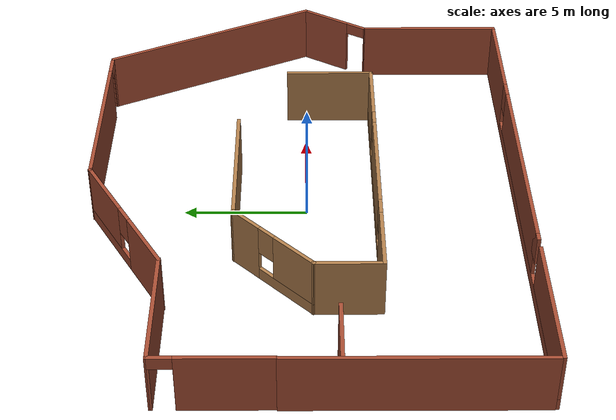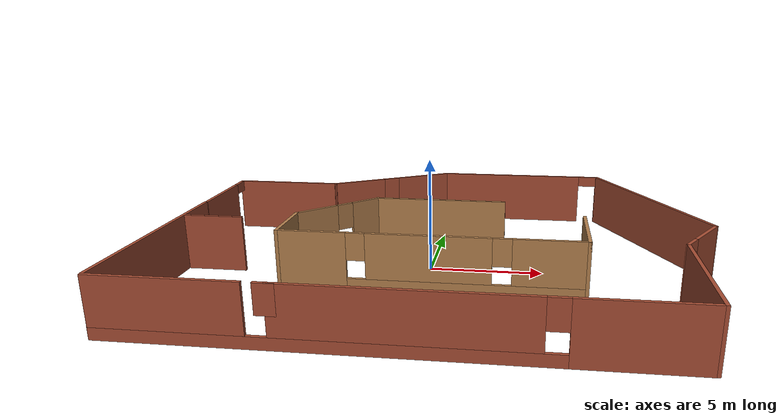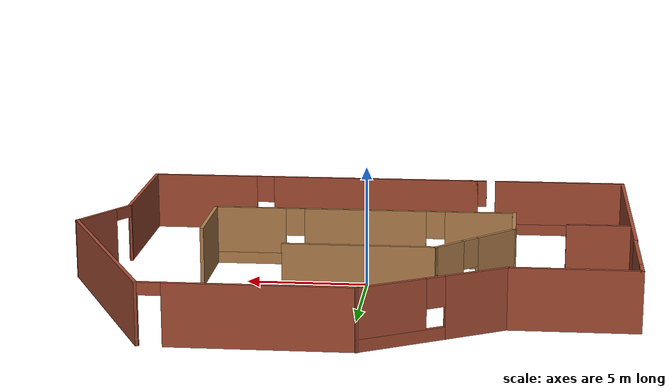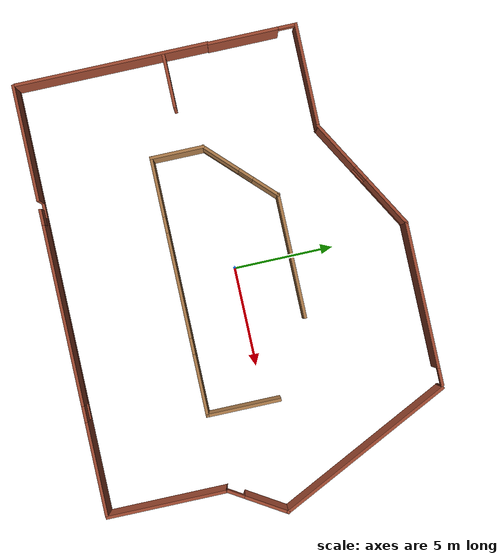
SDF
<?xml version='1.0'?>
<sdf version='1.6'>
  <model name='office'>
    <link name='Wall_10'>
      <pose frame=''>3.71196 8.6392 0 0 -0 0</pose>
      <self_collide>0</self_collide>
      <kinematic>0</kinematic>
      <visual name='Wall_10_Visual_1'>
        <pose frame=''>4.12333 0 1.25 0 -0 0</pose>
        <geometry>
          <box>
            <size>0.003332 0.15 2.5</size>
          </box>
        </geometry>
        <material>
          <script>
            <uri>file://media/materials/scripts/gazebo.material</uri>
            <name>Gazebo/Bricks</name>
          </script>
          <ambient>1 1 1 1</ambient>
          <shader type='pixel'/>
          <diffuse>1 1 1 1</diffuse>
          <specular>0.2 0.2 0.2 1</specular>
          <emissive>0 0 0 1</emissive>
        </material>
        <meta>
          <layer>0</layer>
        </meta>
        <transparency>0</transparency>
        <cast_shadows>1</cast_shadows>
      </visual>
      <visual name='Wall_10_Visual_0'>
        <pose frame=''>-0.451666 0 1.25 0 -0 0</pose>
        <geometry>
          <box>
            <size>7.34667 0.15 2.5</size>
          </box>
        </geometry>
        <material>
          <script>
            <uri>file://media/materials/scripts/gazebo.material</uri>
            <name>Gazebo/Bricks</name>
          </script>
          <ambient>1 1 1 1</ambient>
          <shader type='pixel'/>
          <diffuse>1 1 1 1</diffuse>
          <specular>0.2 0.2 0.2 1</specular>
          <emissive>0 0 0 1</emissive>
        </material>
        <meta>
          <layer>0</layer>
        </meta>
        <transparency>0</transparency>
        <cast_shadows>1</cast_shadows>
      </visual>
      <visual name='Wall_10_Visual_2'>
        <pose frame=''>3.67167 0 2.25 0 -0 0</pose>
        <geometry>
          <box>
            <size>0.9 0.15 0.5</size>
          </box>
        </geometry>
        <material>
          <script>
            <uri>file://media/materials/scripts/gazebo.material</uri>
            <name>Gazebo/Bricks</name>
          </script>
          <ambient>1 1 1 1</ambient>
          <shader type='pixel'/>
          <diffuse>1 1 1 1</diffuse>
          <specular>0.2 0.2 0.2 1</specular>
          <emissive>0 0 0 1</emissive>
        </material>
        <meta>
          <layer>0</layer>
        </meta>
        <transparency>0</transparency>
        <cast_shadows>1</cast_shadows>
      </visual>
      <collision name='Wall_10_Collision_0'>
        <laser_retro>0</laser_retro>
        <max_contacts>10</max_contacts>
        <pose frame=''>-0.451666 0 1.25 0 -0 0</pose>
        <geometry>
          <box>
            <size>7.34667 0.15 2.5</size>
          </box>
        </geometry>
        <surface>
          <friction>
            <ode>
              <mu>1</mu>
              <mu2>1</mu2>
              <fdir1>0 0 0</fdir1>
              <slip1>0</slip1>
              <slip2>0</slip2>
            </ode>
            <torsional>
              <coefficient>1</coefficient>
              <patch_radius>0</patch_radius>
              <surface_radius>0</surface_radius>
              <use_patch_radius>1</use_patch_radius>
              <ode>
                <slip>0</slip>
              </ode>
            </torsional>
          </friction>
          <bounce>
            <restitution_coefficient>0</restitution_coefficient>
            <threshold>1e+06</threshold>
          </bounce>
          <contact>
            <collide_without_contact>0</collide_without_contact>
            <collide_without_contact_bitmask>1</collide_without_contact_bitmask>
            <collide_bitmask>1</collide_bitmask>
            <ode>
              <soft_cfm>0</soft_cfm>
              <soft_erp>0.2</soft_erp>
              <kp>1e+13</kp>
              <kd>1</kd>
              <max_vel>0.01</max_vel>
              <min_depth>0</min_depth>
            </ode>
            <bullet>
              <split_impulse>1</split_impulse>
              <split_impulse_penetration_threshold>-0.01</split_impulse_penetration_threshold>
              <soft_cfm>0</soft_cfm>
              <soft_erp>0.2</soft_erp>
              <kp>1e+13</kp>
              <kd>1</kd>
            </bullet>
          </contact>
        </surface>
      </collision>
      <collision name='Wall_10_Collision_2'>
        <laser_retro>0</laser_retro>
        <max_contacts>10</max_contacts>
        <pose frame=''>3.67167 0 2.25 0 -0 0</pose>
        <geometry>
          <box>
            <size>0.9 0.15 0.5</size>
          </box>
        </geometry>
        <surface>
          <friction>
            <ode>
              <mu>1</mu>
              <mu2>1</mu2>
              <fdir1>0 0 0</fdir1>
              <slip1>0</slip1>
              <slip2>0</slip2>
            </ode>
            <torsional>
              <coefficient>1</coefficient>
              <patch_radius>0</patch_radius>
              <surface_radius>0</surface_radius>
              <use_patch_radius>1</use_patch_radius>
              <ode>
                <slip>0</slip>
              </ode>
            </torsional>
          </friction>
          <bounce>
            <restitution_coefficient>0</restitution_coefficient>
            <threshold>1e+06</threshold>
          </bounce>
          <contact>
            <collide_without_contact>0</collide_without_contact>
            <collide_without_contact_bitmask>1</collide_without_contact_bitmask>
            <collide_bitmask>1</collide_bitmask>
            <ode>
              <soft_cfm>0</soft_cfm>
              <soft_erp>0.2</soft_erp>
              <kp>1e+13</kp>
              <kd>1</kd>
              <max_vel>0.01</max_vel>
              <min_depth>0</min_depth>
            </ode>
            <bullet>
              <split_impulse>1</split_impulse>
              <split_impulse_penetration_threshold>-0.01</split_impulse_penetration_threshold>
              <soft_cfm>0</soft_cfm>
              <soft_erp>0.2</soft_erp>
              <kp>1e+13</kp>
              <kd>1</kd>
            </bullet>
          </contact>
        </surface>
      </collision>
      <collision name='Wall_10_Collision_1'>
        <laser_retro>0</laser_retro>
        <max_contacts>10</max_contacts>
        <pose frame=''>4.12333 0 1.25 0 -0 0</pose>
        <geometry>
          <box>
            <size>0.003332 0.15 2.5</size>
          </box>
        </geometry>
        <surface>
          <friction>
            <ode>
              <mu>1</mu>
              <mu2>1</mu2>
              <fdir1>0 0 0</fdir1>
              <slip1>0</slip1>
              <slip2>0</slip2>
            </ode>
            <torsional>
              <coefficient>1</coefficient>
              <patch_radius>0</patch_radius>
              <surface_radius>0</surface_radius>
              <use_patch_radius>1</use_patch_radius>
              <ode>
                <slip>0</slip>
              </ode>
            </torsional>
          </friction>
          <bounce>
            <restitution_coefficient>0</restitution_coefficient>
            <threshold>1e+06</threshold>
          </bounce>
          <contact>
            <collide_without_contact>0</collide_without_contact>
            <collide_without_contact_bitmask>1</collide_without_contact_bitmask>
            <collide_bitmask>1</collide_bitmask>
            <ode>
              <soft_cfm>0</soft_cfm>
              <soft_erp>0.2</soft_erp>
              <kp>1e+13</kp>
              <kd>1</kd>
              <max_vel>0.01</max_vel>
              <min_depth>0</min_depth>
            </ode>
            <bullet>
              <split_impulse>1</split_impulse>
              <split_impulse_penetration_threshold>-0.01</split_impulse_penetration_threshold>
              <soft_cfm>0</soft_cfm>
              <soft_erp>0.2</soft_erp>
              <kp>1e+13</kp>
              <kd>1</kd>
            </bullet>
          </contact>
        </surface>
      </collision>
    </link>
    <link name='Wall_12'>
      <pose frame=''>10.0538 4.3089 0 0 0 -1.1105</pose>
      <self_collide>0</self_collide>
      <kinematic>0</kinematic>
      <inertial>
        <inertia>
          <ixx>0</ixx>
          <ixy>0</ixy>
          <ixz>0</ixz>
          <iyy>0</iyy>
          <iyz>0</iyz>
          <izz>0</izz>
        </inertia>
        <mass>0</mass>
        <pose frame=''>0 0 0 0 -0 0</pose>
      </inertial>
      <visual name='Wall_12_Visual'>
        <pose frame=''>0 0 1.25 0 -0 0</pose>
        <geometry>
          <box>
            <size>9.75381 0.15 2.5</size>
          </box>
        </geometry>
        <material>
          <script>
            <uri>file://media/materials/scripts/gazebo.material</uri>
            <name>Gazebo/Bricks</name>
          </script>
          <ambient>0.435294 0.796078 0.67451 1</ambient>
          <shader type='pixel'/>
          <diffuse>1 1 1 1</diffuse>
          <specular>0.2 0.2 0.2 1</specular>
          <emissive>0 0 0 1</emissive>
        </material>
        <meta>
          <layer>0</layer>
        </meta>
        <transparency>0</transparency>
        <cast_shadows>1</cast_shadows>
      </visual>
      <collision name='Wall_12_Collision'>
        <laser_retro>0</laser_retro>
        <max_contacts>10</max_contacts>
        <pose frame=''>0 0 1.25 0 -0 0</pose>
        <geometry>
          <box>
            <size>9.75381 0.15 2.5</size>
          </box>
        </geometry>
        <surface>
          <friction>
            <ode>
              <mu>1</mu>
              <mu2>1</mu2>
              <fdir1>0 0 0</fdir1>
              <slip1>0</slip1>
              <slip2>0</slip2>
            </ode>
            <torsional>
              <coefficient>1</coefficient>
              <patch_radius>0</patch_radius>
              <surface_radius>0</surface_radius>
              <use_patch_radius>1</use_patch_radius>
              <ode>
                <slip>0</slip>
              </ode>
            </torsional>
          </friction>
          <bounce>
            <restitution_coefficient>0</restitution_coefficient>
            <threshold>1e+06</threshold>
          </bounce>
          <contact>
            <collide_without_contact>0</collide_without_contact>
            <collide_without_contact_bitmask>1</collide_without_contact_bitmask>
            <collide_bitmask>1</collide_bitmask>
            <ode>
              <soft_cfm>0</soft_cfm>
              <soft_erp>0.2</soft_erp>
              <kp>1e+13</kp>
              <kd>1</kd>
              <max_vel>0.01</max_vel>
              <min_depth>0</min_depth>
            </ode>
            <bullet>
              <split_impulse>1</split_impulse>
              <split_impulse_penetration_threshold>-0.01</split_impulse_penetration_threshold>
              <soft_cfm>0</soft_cfm>
              <soft_erp>0.2</soft_erp>
              <kp>1e+13</kp>
              <kd>1</kd>
            </bullet>
          </contact>
        </surface>
      </collision>
    </link>
    <link name='Wall_14'>
      <pose frame=''>11.3708 -1.34055 0 0 -0 -2.12201</pose>
      <self_collide>0</self_collide>
      <kinematic>0</kinematic>
      <inertial>
        <inertia>
          <ixx>0</ixx>
          <ixy>0</ixy>
          <ixz>0</ixz>
          <iyy>0</iyy>
          <iyz>0</iyz>
          <izz>0</izz>
        </inertia>
        <mass>0</mass>
        <pose frame=''>0 0 0 0 -0 0</pose>
      </inertial>
      <visual name='Wall_14_Visual_2'>
        <pose frame=''>1.13537 0 2.25 0 -0 0</pose>
        <geometry>
          <box>
            <size>0.904766 0.15 0.5</size>
          </box>
        </geometry>
        <material>
          <script>
            <uri>file://media/materials/scripts/gazebo.material</uri>
            <name>Gazebo/Bricks</name>
          </script>
          <ambient>0.435294 0.796078 0.67451 1</ambient>
          <shader type='pixel'/>
          <diffuse>1 1 1 1</diffuse>
          <specular>0.2 0.2 0.2 1</specular>
          <emissive>0 0 0 1</emissive>
        </material>
        <meta>
          <layer>0</layer>
        </meta>
        <transparency>0</transparency>
        <cast_shadows>1</cast_shadows>
      </visual>
      <visual name='Wall_14_Visual_0'>
        <pose frame=''>-0.469815 0 1.25 0 -0 0</pose>
        <geometry>
          <box>
            <size>2.32261 0.15 2.5</size>
          </box>
        </geometry>
        <material>
          <script>
            <uri>file://media/materials/scripts/gazebo.material</uri>
            <name>Gazebo/Bricks</name>
          </script>
          <ambient>0.435294 0.796078 0.67451 1</ambient>
          <shader type='pixel'/>
          <diffuse>1 1 1 1</diffuse>
          <specular>0.2 0.2 0.2 1</specular>
          <emissive>0 0 0 1</emissive>
        </material>
        <meta>
          <layer>0</layer>
        </meta>
        <transparency>0</transparency>
        <cast_shadows>1</cast_shadows>
      </visual>
      <visual name='Wall_14_Visual_1'>
        <pose frame=''>1.60519 0 1.25 0 -0 0</pose>
        <geometry>
          <box>
            <size>0.039702 0.15 2.5</size>
          </box>
        </geometry>
        <material>
          <script>
            <uri>file://media/materials/scripts/gazebo.material</uri>
            <name>Gazebo/Bricks</name>
          </script>
          <ambient>0.435294 0.796078 0.67451 1</ambient>
          <shader type='pixel'/>
          <diffuse>1 1 1 1</diffuse>
          <specular>0.2 0.2 0.2 1</specular>
          <emissive>0 0 0 1</emissive>
        </material>
        <meta>
          <layer>0</layer>
        </meta>
        <transparency>0</transparency>
        <cast_shadows>1</cast_shadows>
      </visual>
      <collision name='Wall_14_Collision_2'>
        <laser_retro>0</laser_retro>
        <max_contacts>10</max_contacts>
        <pose frame=''>1.13537 0 2.25 0 -0 0</pose>
        <geometry>
          <box>
            <size>0.904766 0.15 0.5</size>
          </box>
        </geometry>
        <surface>
          <friction>
            <ode>
              <mu>1</mu>
              <mu2>1</mu2>
              <fdir1>0 0 0</fdir1>
              <slip1>0</slip1>
              <slip2>0</slip2>
            </ode>
            <torsional>
              <coefficient>1</coefficient>
              <patch_radius>0</patch_radius>
              <surface_radius>0</surface_radius>
              <use_patch_radius>1</use_patch_radius>
              <ode>
                <slip>0</slip>
              </ode>
            </torsional>
          </friction>
          <bounce>
            <restitution_coefficient>0</restitution_coefficient>
            <threshold>1e+06</threshold>
          </bounce>
          <contact>
            <collide_without_contact>0</collide_without_contact>
            <collide_without_contact_bitmask>1</collide_without_contact_bitmask>
            <collide_bitmask>1</collide_bitmask>
            <ode>
              <soft_cfm>0</soft_cfm>
              <soft_erp>0.2</soft_erp>
              <kp>1e+13</kp>
              <kd>1</kd>
              <max_vel>0.01</max_vel>
              <min_depth>0</min_depth>
            </ode>
            <bullet>
              <split_impulse>1</split_impulse>
              <split_impulse_penetration_threshold>-0.01</split_impulse_penetration_threshold>
              <soft_cfm>0</soft_cfm>
              <soft_erp>0.2</soft_erp>
              <kp>1e+13</kp>
              <kd>1</kd>
            </bullet>
          </contact>
        </surface>
      </collision>
      <collision name='Wall_14_Collision_1'>
        <laser_retro>0</laser_retro>
        <max_contacts>10</max_contacts>
        <pose frame=''>1.60519 0 1.25 0 -0 0</pose>
        <geometry>
          <box>
            <size>0.039702 0.15 2.5</size>
          </box>
        </geometry>
        <surface>
          <friction>
            <ode>
              <mu>1</mu>
              <mu2>1</mu2>
              <fdir1>0 0 0</fdir1>
              <slip1>0</slip1>
              <slip2>0</slip2>
            </ode>
            <torsional>
              <coefficient>1</coefficient>
              <patch_radius>0</patch_radius>
              <surface_radius>0</surface_radius>
              <use_patch_radius>1</use_patch_radius>
              <ode>
                <slip>0</slip>
              </ode>
            </torsional>
          </friction>
          <bounce>
            <restitution_coefficient>0</restitution_coefficient>
            <threshold>1e+06</threshold>
          </bounce>
          <contact>
            <collide_without_contact>0</collide_without_contact>
            <collide_without_contact_bitmask>1</collide_without_contact_bitmask>
            <collide_bitmask>1</collide_bitmask>
            <ode>
              <soft_cfm>0</soft_cfm>
              <soft_erp>0.2</soft_erp>
              <kp>1e+13</kp>
              <kd>1</kd>
              <max_vel>0.01</max_vel>
              <min_depth>0</min_depth>
            </ode>
            <bullet>
              <split_impulse>1</split_impulse>
              <split_impulse_penetration_threshold>-0.01</split_impulse_penetration_threshold>
              <soft_cfm>0</soft_cfm>
              <soft_erp>0.2</soft_erp>
              <kp>1e+13</kp>
              <kd>1</kd>
            </bullet>
          </contact>
        </surface>
      </collision>
      <collision name='Wall_14_Collision_0'>
        <laser_retro>0</laser_retro>
        <max_contacts>10</max_contacts>
        <pose frame=''>-0.469815 0 1.25 0 -0 0</pose>
        <geometry>
          <box>
            <size>2.32261 0.15 2.5</size>
          </box>
        </geometry>
        <surface>
          <friction>
            <ode>
              <mu>1</mu>
              <mu2>1</mu2>
              <fdir1>0 0 0</fdir1>
              <slip1>0</slip1>
              <slip2>0</slip2>
            </ode>
            <torsional>
              <coefficient>1</coefficient>
              <patch_radius>0</patch_radius>
              <surface_radius>0</surface_radius>
              <use_patch_radius>1</use_patch_radius>
              <ode>
                <slip>0</slip>
              </ode>
            </torsional>
          </friction>
          <bounce>
            <restitution_coefficient>0</restitution_coefficient>
            <threshold>1e+06</threshold>
          </bounce>
          <contact>
            <collide_without_contact>0</collide_without_contact>
            <collide_without_contact_bitmask>1</collide_without_contact_bitmask>
            <collide_bitmask>1</collide_bitmask>
            <ode>
              <soft_cfm>0</soft_cfm>
              <soft_erp>0.2</soft_erp>
              <kp>1e+13</kp>
              <kd>1</kd>
              <max_vel>0.01</max_vel>
              <min_depth>0</min_depth>
            </ode>
            <bullet>
              <split_impulse>1</split_impulse>
              <split_impulse_penetration_threshold>-0.01</split_impulse_penetration_threshold>
              <soft_cfm>0</soft_cfm>
              <soft_erp>0.2</soft_erp>
              <kp>1e+13</kp>
              <kd>1</kd>
            </bullet>
          </contact>
        </surface>
      </collision>
    </link>
    <link name='Wall_15'>
      <pose frame=''>10.5606 -5.72124 0 0 0 -1.5708</pose>
      <self_collide>0</self_collide>
      <kinematic>0</kinematic>
      <visual name='Wall_15_Visual'>
        <pose frame=''>0 0 1.25 0 -0 0</pose>
        <geometry>
          <box>
            <size>6 0.15 2.5</size>
          </box>
        </geometry>
        <material>
          <script>
            <uri>file://media/materials/scripts/gazebo.material</uri>
            <name>Gazebo/Bricks</name>
          </script>
          <ambient>0.435294 0.796078 0.67451 1</ambient>
          <shader type='pixel'/>
          <diffuse>1 1 1 1</diffuse>
          <specular>0.2 0.2 0.2 1</specular>
          <emissive>0 0 0 1</emissive>
        </material>
        <meta>
          <layer>0</layer>
        </meta>
        <transparency>0</transparency>
        <cast_shadows>1</cast_shadows>
      </visual>
      <collision name='Wall_15_Collision'>
        <laser_retro>0</laser_retro>
        <max_contacts>10</max_contacts>
        <pose frame=''>0 0 1.25 0 -0 0</pose>
        <geometry>
          <box>
            <size>6 0.15 2.5</size>
          </box>
        </geometry>
        <surface>
          <friction>
            <ode>
              <mu>1</mu>
              <mu2>1</mu2>
              <fdir1>0 0 0</fdir1>
              <slip1>0</slip1>
              <slip2>0</slip2>
            </ode>
            <torsional>
              <coefficient>1</coefficient>
              <patch_radius>0</patch_radius>
              <surface_radius>0</surface_radius>
              <use_patch_radius>1</use_patch_radius>
              <ode>
                <slip>0</slip>
              </ode>
            </torsional>
          </friction>
          <bounce>
            <restitution_coefficient>0</restitution_coefficient>
            <threshold>1e+06</threshold>
          </bounce>
          <contact>
            <collide_without_contact>0</collide_without_contact>
            <collide_without_contact_bitmask>1</collide_without_contact_bitmask>
            <collide_bitmask>1</collide_bitmask>
            <ode>
              <soft_cfm>0</soft_cfm>
              <soft_erp>0.2</soft_erp>
              <kp>1e+13</kp>
              <kd>1</kd>
              <max_vel>0.01</max_vel>
              <min_depth>0</min_depth>
            </ode>
            <bullet>
              <split_impulse>1</split_impulse>
              <split_impulse_penetration_threshold>-0.01</split_impulse_penetration_threshold>
              <soft_cfm>0</soft_cfm>
              <soft_erp>0.2</soft_erp>
              <kp>1e+13</kp>
              <kd>1</kd>
            </bullet>
          </contact>
        </surface>
      </collision>
    </link>
    <link name='Wall_16'>
      <pose frame=''>-0.257157 -8.66079 0 0 -0 3.14159</pose>
      <self_collide>0</self_collide>
      <kinematic>0</kinematic>
      <inertial>
        <inertia>
          <ixx>0</ixx>
          <ixy>0</ixy>
          <ixz>0</ixz>
          <iyy>0</iyy>
          <iyz>0</iyz>
          <izz>0</izz>
        </inertia>
        <mass>0</mass>
        <pose frame=''>0 0 0 0 -0 0</pose>
      </inertial>
      <visual name='Wall_16_Visual_5'>
        <pose frame=''>4.13509 0 1.9 0 -0 0</pose>
        <geometry>
          <box>
            <size>0.801337 0.15 1.2</size>
          </box>
        </geometry>
        <material>
          <script>
            <uri>file://media/materials/scripts/gazebo.material</uri>
            <name>Gazebo/Bricks</name>
          </script>
          <ambient>0.435294 0.796078 0.67451 1</ambient>
          <shader type='pixel'/>
          <diffuse>1 1 1 1</diffuse>
          <specular>0.2 0.2 0.2 1</specular>
          <emissive>0 0 0 1</emissive>
        </material>
        <meta>
          <layer>0</layer>
        </meta>
        <transparency>0</transparency>
        <cast_shadows>1</cast_shadows>
      </visual>
      <visual name='Wall_16_Visual_0'>
        <pose frame=''>-8.41899 0 1.25 0 -0 0</pose>
        <geometry>
          <box>
            <size>4.66983 0.15 2.5</size>
          </box>
        </geometry>
        <material>
          <script>
            <uri>file://media/materials/scripts/gazebo.material</uri>
            <name>Gazebo/Bricks</name>
          </script>
          <ambient>0.435294 0.796078 0.67451 1</ambient>
          <shader type='pixel'/>
          <diffuse>1 1 1 1</diffuse>
          <specular>0.2 0.2 0.2 1</specular>
          <emissive>0 0 0 1</emissive>
        </material>
        <meta>
          <layer>0</layer>
        </meta>
        <transparency>0</transparency>
        <cast_shadows>1</cast_shadows>
      </visual>
      <visual name='Wall_16_Visual_3'>
        <pose frame=''>7.84255 0 1.5 0 -0 0</pose>
        <geometry>
          <box>
            <size>5.82463 0.15 2</size>
          </box>
        </geometry>
        <material>
          <script>
            <uri>file://media/materials/scripts/gazebo.material</uri>
            <name>Gazebo/Bricks</name>
          </script>
          <ambient>0.435294 0.796078 0.67451 1</ambient>
          <shader type='pixel'/>
          <diffuse>1 1 1 1</diffuse>
          <specular>0.2 0.2 0.2 1</specular>
          <emissive>0 0 0 1</emissive>
        </material>
        <meta>
          <layer>0</layer>
        </meta>
        <transparency>0</transparency>
        <cast_shadows>1</cast_shadows>
      </visual>
      <visual name='Wall_16_Visual_4'>
        <pose frame=''>-5.68797 0 1.9 0 -0 0</pose>
        <geometry>
          <box>
            <size>0.801337 0.15 1.2</size>
          </box>
        </geometry>
        <material>
          <script>
            <uri>file://media/materials/scripts/gazebo.material</uri>
            <name>Gazebo/Bricks</name>
          </script>
          <ambient>0.435294 0.796078 0.67451 1</ambient>
          <shader type='pixel'/>
          <diffuse>1 1 1 1</diffuse>
          <specular>0.2 0.2 0.2 1</specular>
          <emissive>0 0 0 1</emissive>
        </material>
        <meta>
          <layer>0</layer>
        </meta>
        <transparency>0</transparency>
        <cast_shadows>1</cast_shadows>
      </visual>
      <visual name='Wall_16_Visual_2'>
        <pose frame=''>-0.576441 0 1.5 0 -0 0</pose>
        <geometry>
          <box>
            <size>9.43881 0.15 2</size>
          </box>
        </geometry>
        <material>
          <script>
            <uri>file://media/materials/scripts/gazebo.material</uri>
            <name>Gazebo/Bricks</name>
          </script>
          <ambient>0.435294 0.796078 0.67451 1</ambient>
          <shader type='pixel'/>
          <diffuse>1 1 1 1</diffuse>
          <specular>0.2 0.2 0.2 1</specular>
          <emissive>0 0 0 1</emissive>
        </material>
        <meta>
          <layer>0</layer>
        </meta>
        <transparency>0</transparency>
        <cast_shadows>1</cast_shadows>
      </visual>
      <visual name='Wall_16_Visual_1'>
        <pose frame=''>2.33101 0 0.25 0 -0 0</pose>
        <geometry>
          <box>
            <size>16.8662 0.15 0.5</size>
          </box>
        </geometry>
        <material>
          <script>
            <uri>file://media/materials/scripts/gazebo.material</uri>
            <name>Gazebo/Bricks</name>
          </script>
          <ambient>0.435294 0.796078 0.67451 1</ambient>
          <shader type='pixel'/>
          <diffuse>1 1 1 1</diffuse>
          <specular>0.2 0.2 0.2 1</specular>
          <emissive>0 0 0 1</emissive>
        </material>
        <meta>
          <layer>0</layer>
        </meta>
        <transparency>0</transparency>
        <cast_shadows>1</cast_shadows>
      </visual>
      <collision name='Wall_16_Collision_0'>
        <laser_retro>0</laser_retro>
        <max_contacts>10</max_contacts>
        <pose frame=''>-8.41899 0 1.25 0 -0 0</pose>
        <geometry>
          <box>
            <size>4.66983 0.15 2.5</size>
          </box>
        </geometry>
        <surface>
          <friction>
            <ode>
              <mu>1</mu>
              <mu2>1</mu2>
              <fdir1>0 0 0</fdir1>
              <slip1>0</slip1>
              <slip2>0</slip2>
            </ode>
            <torsional>
              <coefficient>1</coefficient>
              <patch_radius>0</patch_radius>
              <surface_radius>0</surface_radius>
              <use_patch_radius>1</use_patch_radius>
              <ode>
                <slip>0</slip>
              </ode>
            </torsional>
          </friction>
          <bounce>
            <restitution_coefficient>0</restitution_coefficient>
            <threshold>1e+06</threshold>
          </bounce>
          <contact>
            <collide_without_contact>0</collide_without_contact>
            <collide_without_contact_bitmask>1</collide_without_contact_bitmask>
            <collide_bitmask>1</collide_bitmask>
            <ode>
              <soft_cfm>0</soft_cfm>
              <soft_erp>0.2</soft_erp>
              <kp>1e+13</kp>
              <kd>1</kd>
              <max_vel>0.01</max_vel>
              <min_depth>0</min_depth>
            </ode>
            <bullet>
              <split_impulse>1</split_impulse>
              <split_impulse_penetration_threshold>-0.01</split_impulse_penetration_threshold>
              <soft_cfm>0</soft_cfm>
              <soft_erp>0.2</soft_erp>
              <kp>1e+13</kp>
              <kd>1</kd>
            </bullet>
          </contact>
        </surface>
      </collision>
      <collision name='Wall_16_Collision_4'>
        <laser_retro>0</laser_retro>
        <max_contacts>10</max_contacts>
        <pose frame=''>-5.68797 0 1.9 0 -0 0</pose>
        <geometry>
          <box>
            <size>0.801337 0.15 1.2</size>
          </box>
        </geometry>
        <surface>
          <friction>
            <ode>
              <mu>1</mu>
              <mu2>1</mu2>
              <fdir1>0 0 0</fdir1>
              <slip1>0</slip1>
              <slip2>0</slip2>
            </ode>
            <torsional>
              <coefficient>1</coefficient>
              <patch_radius>0</patch_radius>
              <surface_radius>0</surface_radius>
              <use_patch_radius>1</use_patch_radius>
              <ode>
                <slip>0</slip>
              </ode>
            </torsional>
          </friction>
          <bounce>
            <restitution_coefficient>0</restitution_coefficient>
            <threshold>1e+06</threshold>
          </bounce>
          <contact>
            <collide_without_contact>0</collide_without_contact>
            <collide_without_contact_bitmask>1</collide_without_contact_bitmask>
            <collide_bitmask>1</collide_bitmask>
            <ode>
              <soft_cfm>0</soft_cfm>
              <soft_erp>0.2</soft_erp>
              <kp>1e+13</kp>
              <kd>1</kd>
              <max_vel>0.01</max_vel>
              <min_depth>0</min_depth>
            </ode>
            <bullet>
              <split_impulse>1</split_impulse>
              <split_impulse_penetration_threshold>-0.01</split_impulse_penetration_threshold>
              <soft_cfm>0</soft_cfm>
              <soft_erp>0.2</soft_erp>
              <kp>1e+13</kp>
              <kd>1</kd>
            </bullet>
          </contact>
        </surface>
      </collision>
      <collision name='Wall_16_Collision_2'>
        <laser_retro>0</laser_retro>
        <max_contacts>10</max_contacts>
        <pose frame=''>-0.576441 0 1.5 0 -0 0</pose>
        <geometry>
          <box>
            <size>9.43881 0.15 2</size>
          </box>
        </geometry>
        <surface>
          <friction>
            <ode>
              <mu>1</mu>
              <mu2>1</mu2>
              <fdir1>0 0 0</fdir1>
              <slip1>0</slip1>
              <slip2>0</slip2>
            </ode>
            <torsional>
              <coefficient>1</coefficient>
              <patch_radius>0</patch_radius>
              <surface_radius>0</surface_radius>
              <use_patch_radius>1</use_patch_radius>
              <ode>
                <slip>0</slip>
              </ode>
            </torsional>
          </friction>
          <bounce>
            <restitution_coefficient>0</restitution_coefficient>
            <threshold>1e+06</threshold>
          </bounce>
          <contact>
            <collide_without_contact>0</collide_without_contact>
            <collide_without_contact_bitmask>1</collide_without_contact_bitmask>
            <collide_bitmask>1</collide_bitmask>
            <ode>
              <soft_cfm>0</soft_cfm>
              <soft_erp>0.2</soft_erp>
              <kp>1e+13</kp>
              <kd>1</kd>
              <max_vel>0.01</max_vel>
              <min_depth>0</min_depth>
            </ode>
            <bullet>
              <split_impulse>1</split_impulse>
              <split_impulse_penetration_threshold>-0.01</split_impulse_penetration_threshold>
              <soft_cfm>0</soft_cfm>
              <soft_erp>0.2</soft_erp>
              <kp>1e+13</kp>
              <kd>1</kd>
            </bullet>
          </contact>
        </surface>
      </collision>
      <collision name='Wall_16_Collision_1'>
        <laser_retro>0</laser_retro>
        <max_contacts>10</max_contacts>
        <pose frame=''>2.33101 0 0.25 0 -0 0</pose>
        <geometry>
          <box>
            <size>16.8662 0.15 0.5</size>
          </box>
        </geometry>
        <surface>
          <friction>
            <ode>
              <mu>1</mu>
              <mu2>1</mu2>
              <fdir1>0 0 0</fdir1>
              <slip1>0</slip1>
              <slip2>0</slip2>
            </ode>
            <torsional>
              <coefficient>1</coefficient>
              <patch_radius>0</patch_radius>
              <surface_radius>0</surface_radius>
              <use_patch_radius>1</use_patch_radius>
              <ode>
                <slip>0</slip>
              </ode>
            </torsional>
          </friction>
          <bounce>
            <restitution_coefficient>0</restitution_coefficient>
            <threshold>1e+06</threshold>
          </bounce>
          <contact>
            <collide_without_contact>0</collide_without_contact>
            <collide_without_contact_bitmask>1</collide_without_contact_bitmask>
            <collide_bitmask>1</collide_bitmask>
            <ode>
              <soft_cfm>0</soft_cfm>
              <soft_erp>0.2</soft_erp>
              <kp>1e+13</kp>
              <kd>1</kd>
              <max_vel>0.01</max_vel>
              <min_depth>0</min_depth>
            </ode>
            <bullet>
              <split_impulse>1</split_impulse>
              <split_impulse_penetration_threshold>-0.01</split_impulse_penetration_threshold>
              <soft_cfm>0</soft_cfm>
              <soft_erp>0.2</soft_erp>
              <kp>1e+13</kp>
              <kd>1</kd>
            </bullet>
          </contact>
        </surface>
      </collision>
      <collision name='Wall_16_Collision_3'>
        <laser_retro>0</laser_retro>
        <max_contacts>10</max_contacts>
        <pose frame=''>7.84255 0 1.5 0 -0 0</pose>
        <geometry>
          <box>
            <size>5.82463 0.15 2</size>
          </box>
        </geometry>
        <surface>
          <friction>
            <ode>
              <mu>1</mu>
              <mu2>1</mu2>
              <fdir1>0 0 0</fdir1>
              <slip1>0</slip1>
              <slip2>0</slip2>
            </ode>
            <torsional>
              <coefficient>1</coefficient>
              <patch_radius>0</patch_radius>
              <surface_radius>0</surface_radius>
              <use_patch_radius>1</use_patch_radius>
              <ode>
                <slip>0</slip>
              </ode>
            </torsional>
          </friction>
          <bounce>
            <restitution_coefficient>0</restitution_coefficient>
            <threshold>1e+06</threshold>
          </bounce>
          <contact>
            <collide_without_contact>0</collide_without_contact>
            <collide_without_contact_bitmask>1</collide_without_contact_bitmask>
            <collide_bitmask>1</collide_bitmask>
            <ode>
              <soft_cfm>0</soft_cfm>
              <soft_erp>0.2</soft_erp>
              <kp>1e+13</kp>
              <kd>1</kd>
              <max_vel>0.01</max_vel>
              <min_depth>0</min_depth>
            </ode>
            <bullet>
              <split_impulse>1</split_impulse>
              <split_impulse_penetration_threshold>-0.01</split_impulse_penetration_threshold>
              <soft_cfm>0</soft_cfm>
              <soft_erp>0.2</soft_erp>
              <kp>1e+13</kp>
              <kd>1</kd>
            </bullet>
          </contact>
        </surface>
      </collision>
      <collision name='Wall_16_Collision_5'>
        <laser_retro>0</laser_retro>
        <max_contacts>10</max_contacts>
        <pose frame=''>4.13509 0 1.9 0 -0 0</pose>
        <geometry>
          <box>
            <size>0.801337 0.15 1.2</size>
          </box>
        </geometry>
        <surface>
          <friction>
            <ode>
              <mu>1</mu>
              <mu2>1</mu2>
              <fdir1>0 0 0</fdir1>
              <slip1>0</slip1>
              <slip2>0</slip2>
            </ode>
            <torsional>
              <coefficient>1</coefficient>
              <patch_radius>0</patch_radius>
              <surface_radius>0</surface_radius>
              <use_patch_radius>1</use_patch_radius>
              <ode>
                <slip>0</slip>
              </ode>
            </torsional>
          </friction>
          <bounce>
            <restitution_coefficient>0</restitution_coefficient>
            <threshold>1e+06</threshold>
          </bounce>
          <contact>
            <collide_without_contact>0</collide_without_contact>
            <collide_without_contact_bitmask>1</collide_without_contact_bitmask>
            <collide_bitmask>1</collide_bitmask>
            <ode>
              <soft_cfm>0</soft_cfm>
              <soft_erp>0.2</soft_erp>
              <kp>1e+13</kp>
              <kd>1</kd>
              <max_vel>0.01</max_vel>
              <min_depth>0</min_depth>
            </ode>
            <bullet>
              <split_impulse>1</split_impulse>
              <split_impulse_penetration_threshold>-0.01</split_impulse_penetration_threshold>
              <soft_cfm>0</soft_cfm>
              <soft_erp>0.2</soft_erp>
              <kp>1e+13</kp>
              <kd>1</kd>
            </bullet>
          </contact>
        </surface>
      </collision>
    </link>
    <link name='Wall_18'>
      <pose frame=''>-10.0712 -1.17835 0 0 -0 3.14159</pose>
      <self_collide>0</self_collide>
      <kinematic>0</kinematic>
      <inertial>
        <inertia>
          <ixx>0</ixx>
          <ixy>0</ixy>
          <ixz>0</ixz>
          <iyy>0</iyy>
          <iyz>0</iyz>
          <izz>0</izz>
        </inertia>
        <mass>0</mass>
        <pose frame=''>0 0 0 0 -0 0</pose>
      </inertial>
      <gravity>1</gravity>
      <visual name='Wall_18_Visual_0'>
        <pose frame=''>-0.488616 0 1.25 0 -0 0</pose>
        <geometry>
          <box>
            <size>2.70441 0.15 2.5</size>
          </box>
        </geometry>
        <material>
          <script>
            <uri>file://media/materials/scripts/gazebo.material</uri>
            <name>Gazebo/Bricks</name>
          </script>
          <ambient>0.435 0.796 0.675 1</ambient>
          <shader type='pixel'>
            <normal_map>__default__</normal_map>
          </shader>
          <diffuse>1 1 1 1</diffuse>
          <specular>0.2 0.2 0.2 1</specular>
          <emissive>0 0 0 1</emissive>
        </material>
        <meta>
          <layer>0</layer>
        </meta>
        <transparency>0</transparency>
        <cast_shadows>1</cast_shadows>
      </visual>
      <collision name='Wall_18_Collision_0'>
        <laser_retro>0</laser_retro>
        <max_contacts>10</max_contacts>
        <pose frame=''>-0.488616 0 1.25 0 -0 0</pose>
        <geometry>
          <box>
            <size>2.70441 0.15 2.5</size>
          </box>
        </geometry>
        <surface>
          <friction>
            <ode>
              <mu>1</mu>
              <mu2>1</mu2>
              <fdir1>0 0 0</fdir1>
              <slip1>0</slip1>
              <slip2>0</slip2>
            </ode>
            <torsional>
              <coefficient>1</coefficient>
              <patch_radius>0</patch_radius>
              <surface_radius>0</surface_radius>
              <use_patch_radius>1</use_patch_radius>
              <ode>
                <slip>0</slip>
              </ode>
            </torsional>
          </friction>
          <bounce>
            <restitution_coefficient>0</restitution_coefficient>
            <threshold>1e+06</threshold>
          </bounce>
          <contact>
            <collide_without_contact>0</collide_without_contact>
            <collide_without_contact_bitmask>1</collide_without_contact_bitmask>
            <collide_bitmask>1</collide_bitmask>
            <ode>
              <soft_cfm>0</soft_cfm>
              <soft_erp>0.2</soft_erp>
              <kp>1e+13</kp>
              <kd>1</kd>
              <max_vel>0.01</max_vel>
              <min_depth>0</min_depth>
            </ode>
            <bullet>
              <split_impulse>1</split_impulse>
              <split_impulse_penetration_threshold>-0.01</split_impulse_penetration_threshold>
              <soft_cfm>0</soft_cfm>
              <soft_erp>0.2</soft_erp>
              <kp>1e+13</kp>
              <kd>1</kd>
            </bullet>
          </contact>
        </surface>
      </collision>
    </link>
    <link name='Wall_21'>
      <pose frame=''>-4.52938 1.29817 0 0 0 -2.35619</pose>
      <self_collide>0</self_collide>
      <kinematic>0</kinematic>
      <visual name='Wall_21_Visual_3'>
        <pose frame=''>-0.314868 0 1.9 0 -0 0</pose>
        <geometry>
          <box>
            <size>0.8 0.15 1.2</size>
          </box>
        </geometry>
        <material>
          <script>
            <uri>file://media/materials/scripts/gazebo.material</uri>
            <name>Gazebo/Wood</name>
          </script>
          <ambient>0.435294 0.796078 0.67451 1</ambient>
          <shader type='pixel'/>
          <diffuse>1 1 1 1</diffuse>
          <specular>0.2 0.2 0.2 1</specular>
          <emissive>0 0 0 1</emissive>
        </material>
        <meta>
          <layer>0</layer>
        </meta>
        <transparency>0</transparency>
        <cast_shadows>1</cast_shadows>
      </visual>
      <visual name='Wall_21_Visual_2'>
        <pose frame=''>1.16757 0 1.5 0 -0 0</pose>
        <geometry>
          <box>
            <size>2.16487 0.15 2</size>
          </box>
        </geometry>
        <material>
          <script>
            <uri>file://media/materials/scripts/gazebo.material</uri>
            <name>Gazebo/Wood</name>
          </script>
          <ambient>0.435294 0.796078 0.67451 1</ambient>
          <shader type='pixel'/>
          <diffuse>1 1 1 1</diffuse>
          <specular>0.2 0.2 0.2 1</specular>
          <emissive>0 0 0 1</emissive>
        </material>
        <meta>
          <layer>0</layer>
        </meta>
        <transparency>0</transparency>
        <cast_shadows>1</cast_shadows>
      </visual>
      <visual name='Wall_21_Visual_1'>
        <pose frame=''>0.767566 0 0.25 0 -0 0</pose>
        <geometry>
          <box>
            <size>2.96487 0.15 0.5</size>
          </box>
        </geometry>
        <material>
          <script>
            <uri>file://media/materials/scripts/gazebo.material</uri>
            <name>Gazebo/Wood</name>
          </script>
          <ambient>0.435294 0.796078 0.67451 1</ambient>
          <shader type='pixel'/>
          <diffuse>1 1 1 1</diffuse>
          <specular>0.2 0.2 0.2 1</specular>
          <emissive>0 0 0 1</emissive>
        </material>
        <meta>
          <layer>0</layer>
        </meta>
        <transparency>0</transparency>
        <cast_shadows>1</cast_shadows>
      </visual>
      <visual name='Wall_21_Visual_0'>
        <pose frame=''>-1.48243 0 1.25 0 -0 0</pose>
        <geometry>
          <box>
            <size>1.53513 0.15 2.5</size>
          </box>
        </geometry>
        <material>
          <script>
            <uri>file://media/materials/scripts/gazebo.material</uri>
            <name>Gazebo/Wood</name>
          </script>
          <ambient>0.435294 0.796078 0.67451 1</ambient>
          <shader type='pixel'/>
          <diffuse>1 1 1 1</diffuse>
          <specular>0.2 0.2 0.2 1</specular>
          <emissive>0 0 0 1</emissive>
        </material>
        <meta>
          <layer>0</layer>
        </meta>
        <transparency>0</transparency>
        <cast_shadows>1</cast_shadows>
      </visual>
      <collision name='Wall_21_Collision_2'>
        <laser_retro>0</laser_retro>
        <max_contacts>10</max_contacts>
        <pose frame=''>1.16757 0 1.5 0 -0 0</pose>
        <geometry>
          <box>
            <size>2.16487 0.15 2</size>
          </box>
        </geometry>
        <surface>
          <friction>
            <ode>
              <mu>1</mu>
              <mu2>1</mu2>
              <fdir1>0 0 0</fdir1>
              <slip1>0</slip1>
              <slip2>0</slip2>
            </ode>
            <torsional>
              <coefficient>1</coefficient>
              <patch_radius>0</patch_radius>
              <surface_radius>0</surface_radius>
              <use_patch_radius>1</use_patch_radius>
              <ode>
                <slip>0</slip>
              </ode>
            </torsional>
          </friction>
          <bounce>
            <restitution_coefficient>0</restitution_coefficient>
            <threshold>1e+06</threshold>
          </bounce>
          <contact>
            <collide_without_contact>0</collide_without_contact>
            <collide_without_contact_bitmask>1</collide_without_contact_bitmask>
            <collide_bitmask>1</collide_bitmask>
            <ode>
              <soft_cfm>0</soft_cfm>
              <soft_erp>0.2</soft_erp>
              <kp>1e+13</kp>
              <kd>1</kd>
              <max_vel>0.01</max_vel>
              <min_depth>0</min_depth>
            </ode>
            <bullet>
              <split_impulse>1</split_impulse>
              <split_impulse_penetration_threshold>-0.01</split_impulse_penetration_threshold>
              <soft_cfm>0</soft_cfm>
              <soft_erp>0.2</soft_erp>
              <kp>1e+13</kp>
              <kd>1</kd>
            </bullet>
          </contact>
        </surface>
      </collision>
      <collision name='Wall_21_Collision_3'>
        <laser_retro>0</laser_retro>
        <max_contacts>10</max_contacts>
        <pose frame=''>-0.314868 0 1.9 0 -0 0</pose>
        <geometry>
          <box>
            <size>0.8 0.15 1.2</size>
          </box>
        </geometry>
        <surface>
          <friction>
            <ode>
              <mu>1</mu>
              <mu2>1</mu2>
              <fdir1>0 0 0</fdir1>
              <slip1>0</slip1>
              <slip2>0</slip2>
            </ode>
            <torsional>
              <coefficient>1</coefficient>
              <patch_radius>0</patch_radius>
              <surface_radius>0</surface_radius>
              <use_patch_radius>1</use_patch_radius>
              <ode>
                <slip>0</slip>
              </ode>
            </torsional>
          </friction>
          <bounce>
            <restitution_coefficient>0</restitution_coefficient>
            <threshold>1e+06</threshold>
          </bounce>
          <contact>
            <collide_without_contact>0</collide_without_contact>
            <collide_without_contact_bitmask>1</collide_without_contact_bitmask>
            <collide_bitmask>1</collide_bitmask>
            <ode>
              <soft_cfm>0</soft_cfm>
              <soft_erp>0.2</soft_erp>
              <kp>1e+13</kp>
              <kd>1</kd>
              <max_vel>0.01</max_vel>
              <min_depth>0</min_depth>
            </ode>
            <bullet>
              <split_impulse>1</split_impulse>
              <split_impulse_penetration_threshold>-0.01</split_impulse_penetration_threshold>
              <soft_cfm>0</soft_cfm>
              <soft_erp>0.2</soft_erp>
              <kp>1e+13</kp>
              <kd>1</kd>
            </bullet>
          </contact>
        </surface>
      </collision>
      <collision name='Wall_21_Collision_1'>
        <laser_retro>0</laser_retro>
        <max_contacts>10</max_contacts>
        <pose frame=''>0.767566 0 0.25 0 -0 0</pose>
        <geometry>
          <box>
            <size>2.96487 0.15 0.5</size>
          </box>
        </geometry>
        <surface>
          <friction>
            <ode>
              <mu>1</mu>
              <mu2>1</mu2>
              <fdir1>0 0 0</fdir1>
              <slip1>0</slip1>
              <slip2>0</slip2>
            </ode>
            <torsional>
              <coefficient>1</coefficient>
              <patch_radius>0</patch_radius>
              <surface_radius>0</surface_radius>
              <use_patch_radius>1</use_patch_radius>
              <ode>
                <slip>0</slip>
              </ode>
            </torsional>
          </friction>
          <bounce>
            <restitution_coefficient>0</restitution_coefficient>
            <threshold>1e+06</threshold>
          </bounce>
          <contact>
            <collide_without_contact>0</collide_without_contact>
            <collide_without_contact_bitmask>1</collide_without_contact_bitmask>
            <collide_bitmask>1</collide_bitmask>
            <ode>
              <soft_cfm>0</soft_cfm>
              <soft_erp>0.2</soft_erp>
              <kp>1e+13</kp>
              <kd>1</kd>
              <max_vel>0.01</max_vel>
              <min_depth>0</min_depth>
            </ode>
            <bullet>
              <split_impulse>1</split_impulse>
              <split_impulse_penetration_threshold>-0.01</split_impulse_penetration_threshold>
              <soft_cfm>0</soft_cfm>
              <soft_erp>0.2</soft_erp>
              <kp>1e+13</kp>
              <kd>1</kd>
            </bullet>
          </contact>
        </surface>
      </collision>
      <collision name='Wall_21_Collision_0'>
        <laser_retro>0</laser_retro>
        <max_contacts>10</max_contacts>
        <pose frame=''>-1.48243 0 1.25 0 -0 0</pose>
        <geometry>
          <box>
            <size>1.53513 0.15 2.5</size>
          </box>
        </geometry>
        <surface>
          <friction>
            <ode>
              <mu>1</mu>
              <mu2>1</mu2>
              <fdir1>0 0 0</fdir1>
              <slip1>0</slip1>
              <slip2>0</slip2>
            </ode>
            <torsional>
              <coefficient>1</coefficient>
              <patch_radius>0</patch_radius>
              <surface_radius>0</surface_radius>
              <use_patch_radius>1</use_patch_radius>
              <ode>
                <slip>0</slip>
              </ode>
            </torsional>
          </friction>
          <bounce>
            <restitution_coefficient>0</restitution_coefficient>
            <threshold>1e+06</threshold>
          </bounce>
          <contact>
            <collide_without_contact>0</collide_without_contact>
            <collide_without_contact_bitmask>1</collide_without_contact_bitmask>
            <collide_bitmask>1</collide_bitmask>
            <ode>
              <soft_cfm>0</soft_cfm>
              <soft_erp>0.2</soft_erp>
              <kp>1e+13</kp>
              <kd>1</kd>
              <max_vel>0.01</max_vel>
              <min_depth>0</min_depth>
            </ode>
            <bullet>
              <split_impulse>1</split_impulse>
              <split_impulse_penetration_threshold>-0.01</split_impulse_penetration_threshold>
              <soft_cfm>0</soft_cfm>
              <soft_erp>0.2</soft_erp>
              <kp>1e+13</kp>
              <kd>1</kd>
            </bullet>
          </contact>
        </surface>
      </collision>
    </link>
    <link name='Wall_22'>
      <pose frame=''>-6.06734 -1.53979 0 0 0 -1.5708</pose>
      <self_collide>0</self_collide>
      <kinematic>0</kinematic>
      <visual name='Wall_22_Visual'>
        <pose frame=''>0 0 1.25 0 -0 0</pose>
        <geometry>
          <box>
            <size>2.75 0.15 2.5</size>
          </box>
        </geometry>
        <material>
          <script>
            <uri>file://media/materials/scripts/gazebo.material</uri>
            <name>Gazebo/Wood</name>
          </script>
          <ambient>0.435294 0.796078 0.67451 1</ambient>
          <shader type='pixel'/>
          <diffuse>1 1 1 1</diffuse>
          <specular>0.2 0.2 0.2 1</specular>
          <emissive>0 0 0 1</emissive>
        </material>
        <meta>
          <layer>0</layer>
        </meta>
        <transparency>0</transparency>
        <cast_shadows>1</cast_shadows>
      </visual>
      <collision name='Wall_22_Collision'>
        <laser_retro>0</laser_retro>
        <max_contacts>10</max_contacts>
        <pose frame=''>0 0 1.25 0 -0 0</pose>
        <geometry>
          <box>
            <size>2.75 0.15 2.5</size>
          </box>
        </geometry>
        <surface>
          <friction>
            <ode>
              <mu>1</mu>
              <mu2>1</mu2>
              <fdir1>0 0 0</fdir1>
              <slip1>0</slip1>
              <slip2>0</slip2>
            </ode>
            <torsional>
              <coefficient>1</coefficient>
              <patch_radius>0</patch_radius>
              <surface_radius>0</surface_radius>
              <use_patch_radius>1</use_patch_radius>
              <ode>
                <slip>0</slip>
              </ode>
            </torsional>
          </friction>
          <bounce>
            <restitution_coefficient>0</restitution_coefficient>
            <threshold>1e+06</threshold>
          </bounce>
          <contact>
            <collide_without_contact>0</collide_without_contact>
            <collide_without_contact_bitmask>1</collide_without_contact_bitmask>
            <collide_bitmask>1</collide_bitmask>
            <ode>
              <soft_cfm>0</soft_cfm>
              <soft_erp>0.2</soft_erp>
              <kp>1e+13</kp>
              <kd>1</kd>
              <max_vel>0.01</max_vel>
              <min_depth>0</min_depth>
            </ode>
            <bullet>
              <split_impulse>1</split_impulse>
              <split_impulse_penetration_threshold>-0.01</split_impulse_penetration_threshold>
              <soft_cfm>0</soft_cfm>
              <soft_erp>0.2</soft_erp>
              <kp>1e+13</kp>
              <kd>1</kd>
            </bullet>
          </contact>
        </surface>
      </collision>
    </link>
    <link name='Wall_23'>
      <pose frame=''>0.357662 -2.83979 0 0 -0 0</pose>
      <self_collide>0</self_collide>
      <kinematic>0</kinematic>
      <visual name='Wall_23_Visual_0'>
        <pose frame=''>-4.98806 0 1.25 0 -0 0</pose>
        <geometry>
          <box>
            <size>3.02388 0.15 2.5</size>
          </box>
        </geometry>
        <material>
          <script>
            <uri>file://media/materials/scripts/gazebo.material</uri>
            <name>Gazebo/Wood</name>
          </script>
          <ambient>0.435294 0.796078 0.67451 1</ambient>
          <shader type='pixel'/>
          <diffuse>1 1 1 1</diffuse>
          <specular>0.2 0.2 0.2 1</specular>
          <emissive>0 0 0 1</emissive>
        </material>
        <meta>
          <layer>0</layer>
        </meta>
        <transparency>0</transparency>
        <cast_shadows>1</cast_shadows>
      </visual>
      <visual name='Wall_23_Visual_1'>
        <pose frame=''>1.51194 0 0.25 0 -0 0</pose>
        <geometry>
          <box>
            <size>9.97612 0.15 0.5</size>
          </box>
        </geometry>
        <material>
          <script>
            <uri>file://media/materials/scripts/gazebo.material</uri>
            <name>Gazebo/Wood</name>
          </script>
          <ambient>0.435294 0.796078 0.67451 1</ambient>
          <shader type='pixel'/>
          <diffuse>1 1 1 1</diffuse>
          <specular>0.2 0.2 0.2 1</specular>
          <emissive>0 0 0 1</emissive>
        </material>
        <meta>
          <layer>0</layer>
        </meta>
        <transparency>0</transparency>
        <cast_shadows>1</cast_shadows>
      </visual>
      <visual name='Wall_23_Visual_2'>
        <pose frame=''>-0.051543 0 1.5 0 -0 0</pose>
        <geometry>
          <box>
            <size>5.24915 0.15 2</size>
          </box>
        </geometry>
        <material>
          <script>
            <uri>file://media/materials/scripts/gazebo.material</uri>
            <name>Gazebo/Wood</name>
          </script>
          <ambient>0.435294 0.796078 0.67451 1</ambient>
          <shader type='pixel'/>
          <diffuse>1 1 1 1</diffuse>
          <specular>0.2 0.2 0.2 1</specular>
          <emissive>0 0 0 1</emissive>
        </material>
        <meta>
          <layer>0</layer>
        </meta>
        <transparency>0</transparency>
        <cast_shadows>1</cast_shadows>
      </visual>
      <visual name='Wall_23_Visual_3'>
        <pose frame=''>4.93652 0 1.5 0 -0 0</pose>
        <geometry>
          <box>
            <size>3.12697 0.15 2</size>
          </box>
        </geometry>
        <material>
          <script>
            <uri>file://media/materials/scripts/gazebo.material</uri>
            <name>Gazebo/Wood</name>
          </script>
          <ambient>0.435294 0.796078 0.67451 1</ambient>
          <shader type='pixel'/>
          <diffuse>1 1 1 1</diffuse>
          <specular>0.2 0.2 0.2 1</specular>
          <emissive>0 0 0 1</emissive>
        </material>
        <meta>
          <layer>0</layer>
        </meta>
        <transparency>0</transparency>
        <cast_shadows>1</cast_shadows>
      </visual>
      <visual name='Wall_23_Visual_4'>
        <pose frame=''>-3.07612 0 1.9 0 -0 0</pose>
        <geometry>
          <box>
            <size>0.8 0.15 1.2</size>
          </box>
        </geometry>
        <material>
          <script>
            <uri>file://media/materials/scripts/gazebo.material</uri>
            <name>Gazebo/Wood</name>
          </script>
          <ambient>0.435294 0.796078 0.67451 1</ambient>
          <shader type='pixel'/>
          <diffuse>1 1 1 1</diffuse>
          <specular>0.2 0.2 0.2 1</specular>
          <emissive>0 0 0 1</emissive>
        </material>
        <meta>
          <layer>0</layer>
        </meta>
        <transparency>0</transparency>
        <cast_shadows>1</cast_shadows>
      </visual>
      <visual name='Wall_23_Visual_5'>
        <pose frame=''>2.97303 0 1.9 0 -0 0</pose>
        <geometry>
          <box>
            <size>0.8 0.15 1.2</size>
          </box>
        </geometry>
        <material>
          <script>
            <uri>file://media/materials/scripts/gazebo.material</uri>
            <name>Gazebo/Wood</name>
          </script>
          <ambient>0.435294 0.796078 0.67451 1</ambient>
          <shader type='pixel'/>
          <diffuse>1 1 1 1</diffuse>
          <specular>0.2 0.2 0.2 1</specular>
          <emissive>0 0 0 1</emissive>
        </material>
        <meta>
          <layer>0</layer>
        </meta>
        <transparency>0</transparency>
        <cast_shadows>1</cast_shadows>
      </visual>
      <collision name='Wall_23_Collision_0'>
        <laser_retro>0</laser_retro>
        <max_contacts>10</max_contacts>
        <pose frame=''>-4.98806 0 1.25 0 -0 0</pose>
        <geometry>
          <box>
            <size>3.02388 0.15 2.5</size>
          </box>
        </geometry>
        <surface>
          <friction>
            <ode>
              <mu>1</mu>
              <mu2>1</mu2>
              <fdir1>0 0 0</fdir1>
              <slip1>0</slip1>
              <slip2>0</slip2>
            </ode>
            <torsional>
              <coefficient>1</coefficient>
              <patch_radius>0</patch_radius>
              <surface_radius>0</surface_radius>
              <use_patch_radius>1</use_patch_radius>
              <ode>
                <slip>0</slip>
              </ode>
            </torsional>
          </friction>
          <bounce>
            <restitution_coefficient>0</restitution_coefficient>
            <threshold>1e+06</threshold>
          </bounce>
          <contact>
            <collide_without_contact>0</collide_without_contact>
            <collide_without_contact_bitmask>1</collide_without_contact_bitmask>
            <collide_bitmask>1</collide_bitmask>
            <ode>
              <soft_cfm>0</soft_cfm>
              <soft_erp>0.2</soft_erp>
              <kp>1e+13</kp>
              <kd>1</kd>
              <max_vel>0.01</max_vel>
              <min_depth>0</min_depth>
            </ode>
            <bullet>
              <split_impulse>1</split_impulse>
              <split_impulse_penetration_threshold>-0.01</split_impulse_penetration_threshold>
              <soft_cfm>0</soft_cfm>
              <soft_erp>0.2</soft_erp>
              <kp>1e+13</kp>
              <kd>1</kd>
            </bullet>
          </contact>
        </surface>
      </collision>
      <collision name='Wall_23_Collision_1'>
        <laser_retro>0</laser_retro>
        <max_contacts>10</max_contacts>
        <pose frame=''>1.51194 0 0.25 0 -0 0</pose>
        <geometry>
          <box>
            <size>9.97612 0.15 0.5</size>
          </box>
        </geometry>
        <surface>
          <friction>
            <ode>
              <mu>1</mu>
              <mu2>1</mu2>
              <fdir1>0 0 0</fdir1>
              <slip1>0</slip1>
              <slip2>0</slip2>
            </ode>
            <torsional>
              <coefficient>1</coefficient>
              <patch_radius>0</patch_radius>
              <surface_radius>0</surface_radius>
              <use_patch_radius>1</use_patch_radius>
              <ode>
                <slip>0</slip>
              </ode>
            </torsional>
          </friction>
          <bounce>
            <restitution_coefficient>0</restitution_coefficient>
            <threshold>1e+06</threshold>
          </bounce>
          <contact>
            <collide_without_contact>0</collide_without_contact>
            <collide_without_contact_bitmask>1</collide_without_contact_bitmask>
            <collide_bitmask>1</collide_bitmask>
            <ode>
              <soft_cfm>0</soft_cfm>
              <soft_erp>0.2</soft_erp>
              <kp>1e+13</kp>
              <kd>1</kd>
              <max_vel>0.01</max_vel>
              <min_depth>0</min_depth>
            </ode>
            <bullet>
              <split_impulse>1</split_impulse>
              <split_impulse_penetration_threshold>-0.01</split_impulse_penetration_threshold>
              <soft_cfm>0</soft_cfm>
              <soft_erp>0.2</soft_erp>
              <kp>1e+13</kp>
              <kd>1</kd>
            </bullet>
          </contact>
        </surface>
      </collision>
      <collision name='Wall_23_Collision_2'>
        <laser_retro>0</laser_retro>
        <max_contacts>10</max_contacts>
        <pose frame=''>-0.051543 0 1.5 0 -0 0</pose>
        <geometry>
          <box>
            <size>5.24915 0.15 2</size>
          </box>
        </geometry>
        <surface>
          <friction>
            <ode>
              <mu>1</mu>
              <mu2>1</mu2>
              <fdir1>0 0 0</fdir1>
              <slip1>0</slip1>
              <slip2>0</slip2>
            </ode>
            <torsional>
              <coefficient>1</coefficient>
              <patch_radius>0</patch_radius>
              <surface_radius>0</surface_radius>
              <use_patch_radius>1</use_patch_radius>
              <ode>
                <slip>0</slip>
              </ode>
            </torsional>
          </friction>
          <bounce>
            <restitution_coefficient>0</restitution_coefficient>
            <threshold>1e+06</threshold>
          </bounce>
          <contact>
            <collide_without_contact>0</collide_without_contact>
            <collide_without_contact_bitmask>1</collide_without_contact_bitmask>
            <collide_bitmask>1</collide_bitmask>
            <ode>
              <soft_cfm>0</soft_cfm>
              <soft_erp>0.2</soft_erp>
              <kp>1e+13</kp>
              <kd>1</kd>
              <max_vel>0.01</max_vel>
              <min_depth>0</min_depth>
            </ode>
            <bullet>
              <split_impulse>1</split_impulse>
              <split_impulse_penetration_threshold>-0.01</split_impulse_penetration_threshold>
              <soft_cfm>0</soft_cfm>
              <soft_erp>0.2</soft_erp>
              <kp>1e+13</kp>
              <kd>1</kd>
            </bullet>
          </contact>
        </surface>
      </collision>
      <collision name='Wall_23_Collision_3'>
        <laser_retro>0</laser_retro>
        <max_contacts>10</max_contacts>
        <pose frame=''>4.93652 0 1.5 0 -0 0</pose>
        <geometry>
          <box>
            <size>3.12697 0.15 2</size>
          </box>
        </geometry>
        <surface>
          <friction>
            <ode>
              <mu>1</mu>
              <mu2>1</mu2>
              <fdir1>0 0 0</fdir1>
              <slip1>0</slip1>
              <slip2>0</slip2>
            </ode>
            <torsional>
              <coefficient>1</coefficient>
              <patch_radius>0</patch_radius>
              <surface_radius>0</surface_radius>
              <use_patch_radius>1</use_patch_radius>
              <ode>
                <slip>0</slip>
              </ode>
            </torsional>
          </friction>
          <bounce>
            <restitution_coefficient>0</restitution_coefficient>
            <threshold>1e+06</threshold>
          </bounce>
          <contact>
            <collide_without_contact>0</collide_without_contact>
            <collide_without_contact_bitmask>1</collide_without_contact_bitmask>
            <collide_bitmask>1</collide_bitmask>
            <ode>
              <soft_cfm>0</soft_cfm>
              <soft_erp>0.2</soft_erp>
              <kp>1e+13</kp>
              <kd>1</kd>
              <max_vel>0.01</max_vel>
              <min_depth>0</min_depth>
            </ode>
            <bullet>
              <split_impulse>1</split_impulse>
              <split_impulse_penetration_threshold>-0.01</split_impulse_penetration_threshold>
              <soft_cfm>0</soft_cfm>
              <soft_erp>0.2</soft_erp>
              <kp>1e+13</kp>
              <kd>1</kd>
            </bullet>
          </contact>
        </surface>
      </collision>
      <collision name='Wall_23_Collision_4'>
        <laser_retro>0</laser_retro>
        <max_contacts>10</max_contacts>
        <pose frame=''>-3.07612 0 1.9 0 -0 0</pose>
        <geometry>
          <box>
            <size>0.8 0.15 1.2</size>
          </box>
        </geometry>
        <surface>
          <friction>
            <ode>
              <mu>1</mu>
              <mu2>1</mu2>
              <fdir1>0 0 0</fdir1>
              <slip1>0</slip1>
              <slip2>0</slip2>
            </ode>
            <torsional>
              <coefficient>1</coefficient>
              <patch_radius>0</patch_radius>
              <surface_radius>0</surface_radius>
              <use_patch_radius>1</use_patch_radius>
              <ode>
                <slip>0</slip>
              </ode>
            </torsional>
          </friction>
          <bounce>
            <restitution_coefficient>0</restitution_coefficient>
            <threshold>1e+06</threshold>
          </bounce>
          <contact>
            <collide_without_contact>0</collide_without_contact>
            <collide_without_contact_bitmask>1</collide_without_contact_bitmask>
            <collide_bitmask>1</collide_bitmask>
            <ode>
              <soft_cfm>0</soft_cfm>
              <soft_erp>0.2</soft_erp>
              <kp>1e+13</kp>
              <kd>1</kd>
              <max_vel>0.01</max_vel>
              <min_depth>0</min_depth>
            </ode>
            <bullet>
              <split_impulse>1</split_impulse>
              <split_impulse_penetration_threshold>-0.01</split_impulse_penetration_threshold>
              <soft_cfm>0</soft_cfm>
              <soft_erp>0.2</soft_erp>
              <kp>1e+13</kp>
              <kd>1</kd>
            </bullet>
          </contact>
        </surface>
      </collision>
      <collision name='Wall_23_Collision_5'>
        <laser_retro>0</laser_retro>
        <max_contacts>10</max_contacts>
        <pose frame=''>2.97303 0 1.9 0 -0 0</pose>
        <geometry>
          <box>
            <size>0.8 0.15 1.2</size>
          </box>
        </geometry>
        <surface>
          <friction>
            <ode>
              <mu>1</mu>
              <mu2>1</mu2>
              <fdir1>0 0 0</fdir1>
              <slip1>0</slip1>
              <slip2>0</slip2>
            </ode>
            <torsional>
              <coefficient>1</coefficient>
              <patch_radius>0</patch_radius>
              <surface_radius>0</surface_radius>
              <use_patch_radius>1</use_patch_radius>
              <ode>
                <slip>0</slip>
              </ode>
            </torsional>
          </friction>
          <bounce>
            <restitution_coefficient>0</restitution_coefficient>
            <threshold>1e+06</threshold>
          </bounce>
          <contact>
            <collide_without_contact>0</collide_without_contact>
            <collide_without_contact_bitmask>1</collide_without_contact_bitmask>
            <collide_bitmask>1</collide_bitmask>
            <ode>
              <soft_cfm>0</soft_cfm>
              <soft_erp>0.2</soft_erp>
              <kp>1e+13</kp>
              <kd>1</kd>
              <max_vel>0.01</max_vel>
              <min_depth>0</min_depth>
            </ode>
            <bullet>
              <split_impulse>1</split_impulse>
              <split_impulse_penetration_threshold>-0.01</split_impulse_penetration_threshold>
              <soft_cfm>0</soft_cfm>
              <soft_erp>0.2</soft_erp>
              <kp>1e+13</kp>
              <kd>1</kd>
            </bullet>
          </contact>
        </surface>
      </collision>
    </link>
    <link name='Wall_24'>
      <pose frame=''>6.78266 -1.03979 0 0 -0 1.5708</pose>
      <self_collide>0</self_collide>
      <kinematic>0</kinematic>
      <visual name='Wall_24_Visual'>
        <pose frame=''>0 0 1.25 0 -0 0</pose>
        <geometry>
          <box>
            <size>3.75 0.15 2.5</size>
          </box>
        </geometry>
        <material>
          <script>
            <uri>file://media/materials/scripts/gazebo.material</uri>
            <name>Gazebo/Wood</name>
          </script>
          <ambient>0.435294 0.796078 0.67451 1</ambient>
          <shader type='pixel'/>
          <diffuse>1 1 1 1</diffuse>
          <specular>0.2 0.2 0.2 1</specular>
          <emissive>0 0 0 1</emissive>
        </material>
        <meta>
          <layer>0</layer>
        </meta>
        <transparency>0</transparency>
        <cast_shadows>1</cast_shadows>
      </visual>
      <collision name='Wall_24_Collision'>
        <laser_retro>0</laser_retro>
        <max_contacts>10</max_contacts>
        <pose frame=''>0 0 1.25 0 -0 0</pose>
        <geometry>
          <box>
            <size>3.75 0.15 2.5</size>
          </box>
        </geometry>
        <surface>
          <friction>
            <ode>
              <mu>1</mu>
              <mu2>1</mu2>
              <fdir1>0 0 0</fdir1>
              <slip1>0</slip1>
              <slip2>0</slip2>
            </ode>
            <torsional>
              <coefficient>1</coefficient>
              <patch_radius>0</patch_radius>
              <surface_radius>0</surface_radius>
              <use_patch_radius>1</use_patch_radius>
              <ode>
                <slip>0</slip>
              </ode>
            </torsional>
          </friction>
          <bounce>
            <restitution_coefficient>0</restitution_coefficient>
            <threshold>1e+06</threshold>
          </bounce>
          <contact>
            <collide_without_contact>0</collide_without_contact>
            <collide_without_contact_bitmask>1</collide_without_contact_bitmask>
            <collide_bitmask>1</collide_bitmask>
            <ode>
              <soft_cfm>0</soft_cfm>
              <soft_erp>0.2</soft_erp>
              <kp>1e+13</kp>
              <kd>1</kd>
              <max_vel>0.01</max_vel>
              <min_depth>0</min_depth>
            </ode>
            <bullet>
              <split_impulse>1</split_impulse>
              <split_impulse_penetration_threshold>-0.01</split_impulse_penetration_threshold>
              <soft_cfm>0</soft_cfm>
              <soft_erp>0.2</soft_erp>
              <kp>1e+13</kp>
              <kd>1</kd>
            </bullet>
          </contact>
        </surface>
      </collision>
    </link>
    <link name='Wall_27'>
      <pose frame=''>0.058577 2.83612 0 0 -0 0</pose>
      <self_collide>0</self_collide>
      <kinematic>0</kinematic>
      <visual name='Wall_27_Visual'>
        <pose frame=''>0 0 1.25 0 -0 0</pose>
        <geometry>
          <box>
            <size>6.25 0.15 2.5</size>
          </box>
        </geometry>
        <material>
          <script>
            <uri>file://media/materials/scripts/gazebo.material</uri>
            <name>Gazebo/Wood</name>
          </script>
          <ambient>0.435294 0.796078 0.67451 1</ambient>
          <shader type='pixel'/>
          <diffuse>1 1 1 1</diffuse>
          <specular>0.2 0.2 0.2 1</specular>
          <emissive>0 0 0 1</emissive>
        </material>
        <meta>
          <layer>0</layer>
        </meta>
        <transparency>0</transparency>
        <cast_shadows>1</cast_shadows>
      </visual>
      <collision name='Wall_27_Collision'>
        <laser_retro>0</laser_retro>
        <max_contacts>10</max_contacts>
        <pose frame=''>0 0 1.25 0 -0 0</pose>
        <geometry>
          <box>
            <size>6.25 0.15 2.5</size>
          </box>
        </geometry>
        <surface>
          <friction>
            <ode>
              <mu>1</mu>
              <mu2>1</mu2>
              <fdir1>0 0 0</fdir1>
              <slip1>0</slip1>
              <slip2>0</slip2>
            </ode>
            <torsional>
              <coefficient>1</coefficient>
              <patch_radius>0</patch_radius>
              <surface_radius>0</surface_radius>
              <use_patch_radius>1</use_patch_radius>
              <ode>
                <slip>0</slip>
              </ode>
            </torsional>
          </friction>
          <bounce>
            <restitution_coefficient>0</restitution_coefficient>
            <threshold>1e+06</threshold>
          </bounce>
          <contact>
            <collide_without_contact>0</collide_without_contact>
            <collide_without_contact_bitmask>1</collide_without_contact_bitmask>
            <collide_bitmask>1</collide_bitmask>
            <ode>
              <soft_cfm>0</soft_cfm>
              <soft_erp>0.2</soft_erp>
              <kp>1e+13</kp>
              <kd>1</kd>
              <max_vel>0.01</max_vel>
              <min_depth>0</min_depth>
            </ode>
            <bullet>
              <split_impulse>1</split_impulse>
              <split_impulse_penetration_threshold>-0.01</split_impulse_penetration_threshold>
              <soft_cfm>0</soft_cfm>
              <soft_erp>0.2</soft_erp>
              <kp>1e+13</kp>
              <kd>1</kd>
            </bullet>
          </contact>
        </surface>
      </collision>
    </link>
    <link name='Wall_5_clone'>
      <pose frame=''>-10.9673 -3.76778 0 0 -0 1.5708</pose>
      <self_collide>0</self_collide>
      <kinematic>0</kinematic>
      <inertial>
        <inertia>
          <ixx>0</ixx>
          <ixy>0</ixy>
          <ixz>0</ixz>
          <iyy>0</iyy>
          <iyz>0</iyz>
          <izz>0</izz>
        </inertia>
        <mass>0</mass>
        <pose frame=''>0 0 0 0 -0 0</pose>
      </inertial>
      <visual name='Wall_5_Visual'>
        <pose frame=''>0 0 1.25 0 -0 0</pose>
        <geometry>
          <box>
            <size>9.67537 0.15 2.5</size>
          </box>
        </geometry>
        <material>
          <script>
            <uri>file://media/materials/scripts/gazebo.material</uri>
            <name>Gazebo/Bricks</name>
          </script>
          <ambient>0.435294 0.796078 0.67451 1</ambient>
          <shader type='pixel'/>
          <diffuse>1 1 1 1</diffuse>
          <specular>0.2 0.2 0.2 1</specular>
          <emissive>0 0 0 1</emissive>
        </material>
        <meta>
          <layer>0</layer>
        </meta>
        <transparency>0</transparency>
        <cast_shadows>1</cast_shadows>
      </visual>
      <collision name='Wall_5_Collision'>
        <laser_retro>0</laser_retro>
        <max_contacts>10</max_contacts>
        <pose frame=''>0 0 1.25 0 -0 0</pose>
        <geometry>
          <box>
            <size>9.67537 0.15 2.5</size>
          </box>
        </geometry>
        <surface>
          <friction>
            <ode>
              <mu>1</mu>
              <mu2>1</mu2>
              <fdir1>0 0 0</fdir1>
              <slip1>0</slip1>
              <slip2>0</slip2>
            </ode>
            <torsional>
              <coefficient>1</coefficient>
              <patch_radius>0</patch_radius>
              <surface_radius>0</surface_radius>
              <use_patch_radius>1</use_patch_radius>
              <ode>
                <slip>0</slip>
              </ode>
            </torsional>
          </friction>
          <bounce>
            <restitution_coefficient>0</restitution_coefficient>
            <threshold>1e+06</threshold>
          </bounce>
          <contact>
            <collide_without_contact>0</collide_without_contact>
            <collide_without_contact_bitmask>1</collide_without_contact_bitmask>
            <collide_bitmask>1</collide_bitmask>
            <ode>
              <soft_cfm>0</soft_cfm>
              <soft_erp>0.2</soft_erp>
              <kp>1e+13</kp>
              <kd>1</kd>
              <max_vel>0.01</max_vel>
              <min_depth>0</min_depth>
            </ode>
            <bullet>
              <split_impulse>1</split_impulse>
              <split_impulse_penetration_threshold>-0.01</split_impulse_penetration_threshold>
              <soft_cfm>0</soft_cfm>
              <soft_erp>0.2</soft_erp>
              <kp>1e+13</kp>
              <kd>1</kd>
            </bullet>
          </contact>
        </surface>
      </collision>
    </link>
    <link name='Wall_7'>
      <pose frame=''>-10.9373 3.2892 0 0 -0 1.5708</pose>
      <self_collide>0</self_collide>
      <kinematic>0</kinematic>
      <visual name='Wall_7_Visual_0'>
        <pose frame=''>-0.480218 0 1.25 0 -0 0</pose>
        <geometry>
          <box>
            <size>3.53957 0.15 2.5</size>
          </box>
        </geometry>
        <material>
          <script>
            <uri>file://media/materials/scripts/gazebo.material</uri>
            <name>Gazebo/Bricks</name>
          </script>
          <ambient>0.435294 0.796078 0.67451 1</ambient>
          <shader type='pixel'/>
          <diffuse>1 1 1 1</diffuse>
          <specular>0.2 0.2 0.2 1</specular>
          <emissive>0 0 0 1</emissive>
        </material>
        <meta>
          <layer>0</layer>
        </meta>
        <transparency>0</transparency>
        <cast_shadows>1</cast_shadows>
      </visual>
      <visual name='Wall_7_Visual_1'>
        <pose frame=''>2.21978 0 1.25 0 -0 0</pose>
        <geometry>
          <box>
            <size>0.060435 0.15 2.5</size>
          </box>
        </geometry>
        <material>
          <script>
            <uri>file://media/materials/scripts/gazebo.material</uri>
            <name>Gazebo/Bricks</name>
          </script>
          <ambient>0.435294 0.796078 0.67451 1</ambient>
          <shader type='pixel'/>
          <diffuse>1 1 1 1</diffuse>
          <specular>0.2 0.2 0.2 1</specular>
          <emissive>0 0 0 1</emissive>
        </material>
        <meta>
          <layer>0</layer>
        </meta>
        <transparency>0</transparency>
        <cast_shadows>1</cast_shadows>
      </visual>
      <visual name='Wall_7_Visual_2'>
        <pose frame=''>1.73957 0 2.25 0 -0 0</pose>
        <geometry>
          <box>
            <size>0.9 0.15 0.5</size>
          </box>
        </geometry>
        <material>
          <script>
            <uri>file://media/materials/scripts/gazebo.material</uri>
            <name>Gazebo/Bricks</name>
          </script>
          <ambient>0.435294 0.796078 0.67451 1</ambient>
          <shader type='pixel'/>
          <diffuse>1 1 1 1</diffuse>
          <specular>0.2 0.2 0.2 1</specular>
          <emissive>0 0 0 1</emissive>
        </material>
        <meta>
          <layer>0</layer>
        </meta>
        <transparency>0</transparency>
        <cast_shadows>1</cast_shadows>
      </visual>
      <collision name='Wall_7_Collision_0'>
        <laser_retro>0</laser_retro>
        <max_contacts>10</max_contacts>
        <pose frame=''>-0.480218 0 1.25 0 -0 0</pose>
        <geometry>
          <box>
            <size>3.53957 0.15 2.5</size>
          </box>
        </geometry>
        <surface>
          <friction>
            <ode>
              <mu>1</mu>
              <mu2>1</mu2>
              <fdir1>0 0 0</fdir1>
              <slip1>0</slip1>
              <slip2>0</slip2>
            </ode>
            <torsional>
              <coefficient>1</coefficient>
              <patch_radius>0</patch_radius>
              <surface_radius>0</surface_radius>
              <use_patch_radius>1</use_patch_radius>
              <ode>
                <slip>0</slip>
              </ode>
            </torsional>
          </friction>
          <bounce>
            <restitution_coefficient>0</restitution_coefficient>
            <threshold>1e+06</threshold>
          </bounce>
          <contact>
            <collide_without_contact>0</collide_without_contact>
            <collide_without_contact_bitmask>1</collide_without_contact_bitmask>
            <collide_bitmask>1</collide_bitmask>
            <ode>
              <soft_cfm>0</soft_cfm>
              <soft_erp>0.2</soft_erp>
              <kp>1e+13</kp>
              <kd>1</kd>
              <max_vel>0.01</max_vel>
              <min_depth>0</min_depth>
            </ode>
            <bullet>
              <split_impulse>1</split_impulse>
              <split_impulse_penetration_threshold>-0.01</split_impulse_penetration_threshold>
              <soft_cfm>0</soft_cfm>
              <soft_erp>0.2</soft_erp>
              <kp>1e+13</kp>
              <kd>1</kd>
            </bullet>
          </contact>
        </surface>
      </collision>
      <collision name='Wall_7_Collision_1'>
        <laser_retro>0</laser_retro>
        <max_contacts>10</max_contacts>
        <pose frame=''>2.21978 0 1.25 0 -0 0</pose>
        <geometry>
          <box>
            <size>0.060435 0.15 2.5</size>
          </box>
        </geometry>
        <surface>
          <friction>
            <ode>
              <mu>1</mu>
              <mu2>1</mu2>
              <fdir1>0 0 0</fdir1>
              <slip1>0</slip1>
              <slip2>0</slip2>
            </ode>
            <torsional>
              <coefficient>1</coefficient>
              <patch_radius>0</patch_radius>
              <surface_radius>0</surface_radius>
              <use_patch_radius>1</use_patch_radius>
              <ode>
                <slip>0</slip>
              </ode>
            </torsional>
          </friction>
          <bounce>
            <restitution_coefficient>0</restitution_coefficient>
            <threshold>1e+06</threshold>
          </bounce>
          <contact>
            <collide_without_contact>0</collide_without_contact>
            <collide_without_contact_bitmask>1</collide_without_contact_bitmask>
            <collide_bitmask>1</collide_bitmask>
            <ode>
              <soft_cfm>0</soft_cfm>
              <soft_erp>0.2</soft_erp>
              <kp>1e+13</kp>
              <kd>1</kd>
              <max_vel>0.01</max_vel>
              <min_depth>0</min_depth>
            </ode>
            <bullet>
              <split_impulse>1</split_impulse>
              <split_impulse_penetration_threshold>-0.01</split_impulse_penetration_threshold>
              <soft_cfm>0</soft_cfm>
              <soft_erp>0.2</soft_erp>
              <kp>1e+13</kp>
              <kd>1</kd>
            </bullet>
          </contact>
        </surface>
      </collision>
      <collision name='Wall_7_Collision_2'>
        <laser_retro>0</laser_retro>
        <max_contacts>10</max_contacts>
        <pose frame=''>1.73957 0 2.25 0 -0 0</pose>
        <geometry>
          <box>
            <size>0.9 0.15 0.5</size>
          </box>
        </geometry>
        <surface>
          <friction>
            <ode>
              <mu>1</mu>
              <mu2>1</mu2>
              <fdir1>0 0 0</fdir1>
              <slip1>0</slip1>
              <slip2>0</slip2>
            </ode>
            <torsional>
              <coefficient>1</coefficient>
              <patch_radius>0</patch_radius>
              <surface_radius>0</surface_radius>
              <use_patch_radius>1</use_patch_radius>
              <ode>
                <slip>0</slip>
              </ode>
            </torsional>
          </friction>
          <bounce>
            <restitution_coefficient>0</restitution_coefficient>
            <threshold>1e+06</threshold>
          </bounce>
          <contact>
            <collide_without_contact>0</collide_without_contact>
            <collide_without_contact_bitmask>1</collide_without_contact_bitmask>
            <collide_bitmask>1</collide_bitmask>
            <ode>
              <soft_cfm>0</soft_cfm>
              <soft_erp>0.2</soft_erp>
              <kp>1e+13</kp>
              <kd>1</kd>
              <max_vel>0.01</max_vel>
              <min_depth>0</min_depth>
            </ode>
            <bullet>
              <split_impulse>1</split_impulse>
              <split_impulse_penetration_threshold>-0.01</split_impulse_penetration_threshold>
              <soft_cfm>0</soft_cfm>
              <soft_erp>0.2</soft_erp>
              <kp>1e+13</kp>
              <kd>1</kd>
            </bullet>
          </contact>
        </surface>
      </collision>
    </link>
    <link name='Wall_8'>
      <pose frame=''>-8.3873 5.4642 0 0 -0 0</pose>
      <self_collide>0</self_collide>
      <kinematic>0</kinematic>
      <visual name='Wall_8_Visual'>
        <pose frame=''>0 0 1.25 0 -0 0</pose>
        <geometry>
          <box>
            <size>5.25 0.15 2.5</size>
          </box>
        </geometry>
        <material>
          <script>
            <uri>file://media/materials/scripts/gazebo.material</uri>
            <name>Gazebo/Bricks</name>
          </script>
          <ambient>0.435294 0.796078 0.67451 1</ambient>
          <shader type='pixel'/>
          <diffuse>1 1 1 1</diffuse>
          <specular>0.2 0.2 0.2 1</specular>
          <emissive>0 0 0 1</emissive>
        </material>
        <meta>
          <layer>0</layer>
        </meta>
        <transparency>0</transparency>
        <cast_shadows>1</cast_shadows>
      </visual>
      <collision name='Wall_8_Collision'>
        <laser_retro>0</laser_retro>
        <max_contacts>10</max_contacts>
        <pose frame=''>0 0 1.25 0 -0 0</pose>
        <geometry>
          <box>
            <size>5.25 0.15 2.5</size>
          </box>
        </geometry>
        <surface>
          <friction>
            <ode>
              <mu>1</mu>
              <mu2>1</mu2>
              <fdir1>0 0 0</fdir1>
              <slip1>0</slip1>
              <slip2>0</slip2>
            </ode>
            <torsional>
              <coefficient>1</coefficient>
              <patch_radius>0</patch_radius>
              <surface_radius>0</surface_radius>
              <use_patch_radius>1</use_patch_radius>
              <ode>
                <slip>0</slip>
              </ode>
            </torsional>
          </friction>
          <bounce>
            <restitution_coefficient>0</restitution_coefficient>
            <threshold>1e+06</threshold>
          </bounce>
          <contact>
            <collide_without_contact>0</collide_without_contact>
            <collide_without_contact_bitmask>1</collide_without_contact_bitmask>
            <collide_bitmask>1</collide_bitmask>
            <ode>
              <soft_cfm>0</soft_cfm>
              <soft_erp>0.2</soft_erp>
              <kp>1e+13</kp>
              <kd>1</kd>
              <max_vel>0.01</max_vel>
              <min_depth>0</min_depth>
            </ode>
            <bullet>
              <split_impulse>1</split_impulse>
              <split_impulse_penetration_threshold>-0.01</split_impulse_penetration_threshold>
              <soft_cfm>0</soft_cfm>
              <soft_erp>0.2</soft_erp>
              <kp>1e+13</kp>
              <kd>1</kd>
            </bullet>
          </contact>
        </surface>
      </collision>
    </link>
    <link name='Wall_9'>
      <pose frame=''>-3.08767 7.0517 0 0 -0 0.523599</pose>
      <self_collide>0</self_collide>
      <kinematic>0</kinematic>
      <visual name='Wall_9_Visual_0'>
        <pose frame=''>-1.86997 0 1.25 0 -0 0</pose>
        <geometry>
          <box>
            <size>2.76007 0.15 2.5</size>
          </box>
        </geometry>
        <material>
          <script>
            <uri>file://media/materials/scripts/gazebo.material</uri>
            <name>Gazebo/Bricks</name>
          </script>
          <ambient>0.435294 0.796078 0.67451 1</ambient>
          <shader type='pixel'/>
          <diffuse>1 1 1 1</diffuse>
          <specular>0.2 0.2 0.2 1</specular>
          <emissive>0 0 0 1</emissive>
        </material>
        <meta>
          <layer>0</layer>
        </meta>
        <transparency>0</transparency>
        <cast_shadows>1</cast_shadows>
      </visual>
      <visual name='Wall_9_Visual_1'>
        <pose frame=''>1.38003 0 0.25 0 -0 0</pose>
        <geometry>
          <box>
            <size>3.73993 0.15 0.5</size>
          </box>
        </geometry>
        <material>
          <script>
            <uri>file://media/materials/scripts/gazebo.material</uri>
            <name>Gazebo/Bricks</name>
          </script>
          <ambient>0.435294 0.796078 0.67451 1</ambient>
          <shader type='pixel'/>
          <diffuse>1 1 1 1</diffuse>
          <specular>0.2 0.2 0.2 1</specular>
          <emissive>0 0 0 1</emissive>
        </material>
        <meta>
          <layer>0</layer>
        </meta>
        <transparency>0</transparency>
        <cast_shadows>1</cast_shadows>
      </visual>
      <visual name='Wall_9_Visual_2'>
        <pose frame=''>1.78003 0 1.5 0 -0 0</pose>
        <geometry>
          <box>
            <size>2.93993 0.15 2</size>
          </box>
        </geometry>
        <material>
          <script>
            <uri>file://media/materials/scripts/gazebo.material</uri>
            <name>Gazebo/Bricks</name>
          </script>
          <ambient>0.435294 0.796078 0.67451 1</ambient>
          <shader type='pixel'/>
          <diffuse>1 1 1 1</diffuse>
          <specular>0.2 0.2 0.2 1</specular>
          <emissive>0 0 0 1</emissive>
        </material>
        <meta>
          <layer>0</layer>
        </meta>
        <transparency>0</transparency>
        <cast_shadows>1</cast_shadows>
      </visual>
      <visual name='Wall_9_Visual_3'>
        <pose frame=''>-0.089932 0 1.9 0 -0 0</pose>
        <geometry>
          <box>
            <size>0.8 0.15 1.2</size>
          </box>
        </geometry>
        <material>
          <script>
            <uri>file://media/materials/scripts/gazebo.material</uri>
            <name>Gazebo/Bricks</name>
          </script>
          <ambient>0.435294 0.796078 0.67451 1</ambient>
          <shader type='pixel'/>
          <diffuse>1 1 1 1</diffuse>
          <specular>0.2 0.2 0.2 1</specular>
          <emissive>0 0 0 1</emissive>
        </material>
        <meta>
          <layer>0</layer>
        </meta>
        <transparency>0</transparency>
        <cast_shadows>1</cast_shadows>
      </visual>
      <collision name='Wall_9_Collision_0'>
        <laser_retro>0</laser_retro>
        <max_contacts>10</max_contacts>
        <pose frame=''>-1.86997 0 1.25 0 -0 0</pose>
        <geometry>
          <box>
            <size>2.76007 0.15 2.5</size>
          </box>
        </geometry>
        <surface>
          <friction>
            <ode>
              <mu>1</mu>
              <mu2>1</mu2>
              <fdir1>0 0 0</fdir1>
              <slip1>0</slip1>
              <slip2>0</slip2>
            </ode>
            <torsional>
              <coefficient>1</coefficient>
              <patch_radius>0</patch_radius>
              <surface_radius>0</surface_radius>
              <use_patch_radius>1</use_patch_radius>
              <ode>
                <slip>0</slip>
              </ode>
            </torsional>
          </friction>
          <bounce>
            <restitution_coefficient>0</restitution_coefficient>
            <threshold>1e+06</threshold>
          </bounce>
          <contact>
            <collide_without_contact>0</collide_without_contact>
            <collide_without_contact_bitmask>1</collide_without_contact_bitmask>
            <collide_bitmask>1</collide_bitmask>
            <ode>
              <soft_cfm>0</soft_cfm>
              <soft_erp>0.2</soft_erp>
              <kp>1e+13</kp>
              <kd>1</kd>
              <max_vel>0.01</max_vel>
              <min_depth>0</min_depth>
            </ode>
            <bullet>
              <split_impulse>1</split_impulse>
              <split_impulse_penetration_threshold>-0.01</split_impulse_penetration_threshold>
              <soft_cfm>0</soft_cfm>
              <soft_erp>0.2</soft_erp>
              <kp>1e+13</kp>
              <kd>1</kd>
            </bullet>
          </contact>
        </surface>
      </collision>
      <collision name='Wall_9_Collision_1'>
        <laser_retro>0</laser_retro>
        <max_contacts>10</max_contacts>
        <pose frame=''>1.38003 0 0.25 0 -0 0</pose>
        <geometry>
          <box>
            <size>3.73993 0.15 0.5</size>
          </box>
        </geometry>
        <surface>
          <friction>
            <ode>
              <mu>1</mu>
              <mu2>1</mu2>
              <fdir1>0 0 0</fdir1>
              <slip1>0</slip1>
              <slip2>0</slip2>
            </ode>
            <torsional>
              <coefficient>1</coefficient>
              <patch_radius>0</patch_radius>
              <surface_radius>0</surface_radius>
              <use_patch_radius>1</use_patch_radius>
              <ode>
                <slip>0</slip>
              </ode>
            </torsional>
          </friction>
          <bounce>
            <restitution_coefficient>0</restitution_coefficient>
            <threshold>1e+06</threshold>
          </bounce>
          <contact>
            <collide_without_contact>0</collide_without_contact>
            <collide_without_contact_bitmask>1</collide_without_contact_bitmask>
            <collide_bitmask>1</collide_bitmask>
            <ode>
              <soft_cfm>0</soft_cfm>
              <soft_erp>0.2</soft_erp>
              <kp>1e+13</kp>
              <kd>1</kd>
              <max_vel>0.01</max_vel>
              <min_depth>0</min_depth>
            </ode>
            <bullet>
              <split_impulse>1</split_impulse>
              <split_impulse_penetration_threshold>-0.01</split_impulse_penetration_threshold>
              <soft_cfm>0</soft_cfm>
              <soft_erp>0.2</soft_erp>
              <kp>1e+13</kp>
              <kd>1</kd>
            </bullet>
          </contact>
        </surface>
      </collision>
      <collision name='Wall_9_Collision_2'>
        <laser_retro>0</laser_retro>
        <max_contacts>10</max_contacts>
        <pose frame=''>1.78003 0 1.5 0 -0 0</pose>
        <geometry>
          <box>
            <size>2.93993 0.15 2</size>
          </box>
        </geometry>
        <surface>
          <friction>
            <ode>
              <mu>1</mu>
              <mu2>1</mu2>
              <fdir1>0 0 0</fdir1>
              <slip1>0</slip1>
              <slip2>0</slip2>
            </ode>
            <torsional>
              <coefficient>1</coefficient>
              <patch_radius>0</patch_radius>
              <surface_radius>0</surface_radius>
              <use_patch_radius>1</use_patch_radius>
              <ode>
                <slip>0</slip>
              </ode>
            </torsional>
          </friction>
          <bounce>
            <restitution_coefficient>0</restitution_coefficient>
            <threshold>1e+06</threshold>
          </bounce>
          <contact>
            <collide_without_contact>0</collide_without_contact>
            <collide_without_contact_bitmask>1</collide_without_contact_bitmask>
            <collide_bitmask>1</collide_bitmask>
            <ode>
              <soft_cfm>0</soft_cfm>
              <soft_erp>0.2</soft_erp>
              <kp>1e+13</kp>
              <kd>1</kd>
              <max_vel>0.01</max_vel>
              <min_depth>0</min_depth>
            </ode>
            <bullet>
              <split_impulse>1</split_impulse>
              <split_impulse_penetration_threshold>-0.01</split_impulse_penetration_threshold>
              <soft_cfm>0</soft_cfm>
              <soft_erp>0.2</soft_erp>
              <kp>1e+13</kp>
              <kd>1</kd>
            </bullet>
          </contact>
        </surface>
      </collision>
      <collision name='Wall_9_Collision_3'>
        <laser_retro>0</laser_retro>
        <max_contacts>10</max_contacts>
        <pose frame=''>-0.089932 0 1.9 0 -0 0</pose>
        <geometry>
          <box>
            <size>0.8 0.15 1.2</size>
          </box>
        </geometry>
        <surface>
          <friction>
            <ode>
              <mu>1</mu>
              <mu2>1</mu2>
              <fdir1>0 0 0</fdir1>
              <slip1>0</slip1>
              <slip2>0</slip2>
            </ode>
            <torsional>
              <coefficient>1</coefficient>
              <patch_radius>0</patch_radius>
              <surface_radius>0</surface_radius>
              <use_patch_radius>1</use_patch_radius>
              <ode>
                <slip>0</slip>
              </ode>
            </torsional>
          </friction>
          <bounce>
            <restitution_coefficient>0</restitution_coefficient>
            <threshold>1e+06</threshold>
          </bounce>
          <contact>
            <collide_without_contact>0</collide_without_contact>
            <collide_without_contact_bitmask>1</collide_without_contact_bitmask>
            <collide_bitmask>1</collide_bitmask>
            <ode>
              <soft_cfm>0</soft_cfm>
              <soft_erp>0.2</soft_erp>
              <kp>1e+13</kp>
              <kd>1</kd>
              <max_vel>0.01</max_vel>
              <min_depth>0</min_depth>
            </ode>
            <bullet>
              <split_impulse>1</split_impulse>
              <split_impulse_penetration_threshold>-0.01</split_impulse_penetration_threshold>
              <soft_cfm>0</soft_cfm>
              <soft_erp>0.2</soft_erp>
              <kp>1e+13</kp>
              <kd>1</kd>
            </bullet>
          </contact>
        </surface>
      </collision>
    </link>
    <static>1</static>
    <allow_auto_disable>1</allow_auto_disable>
  </model>
</sdf>
